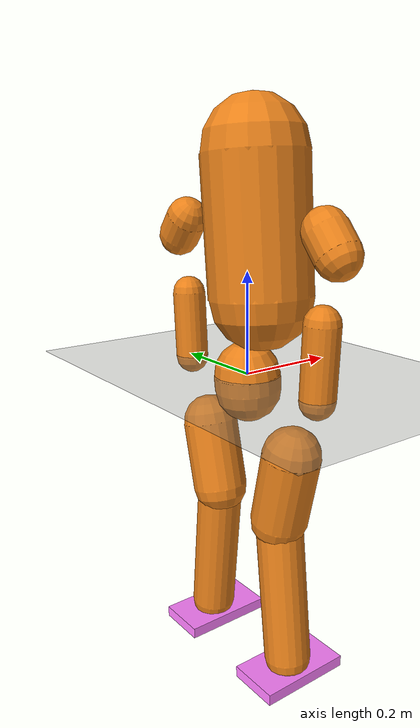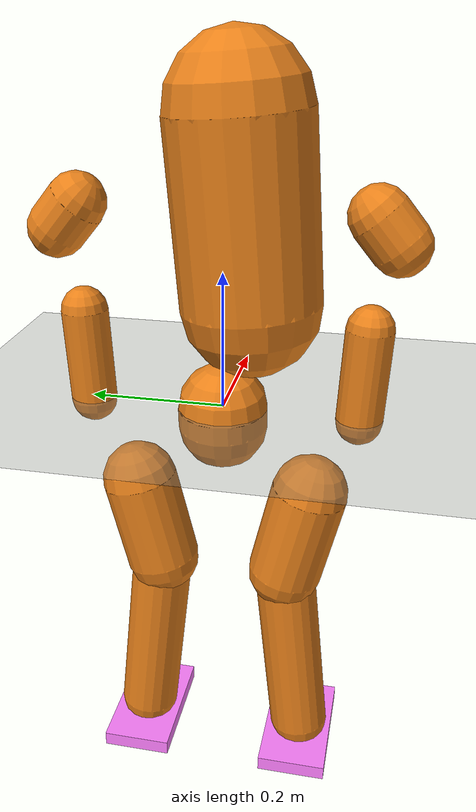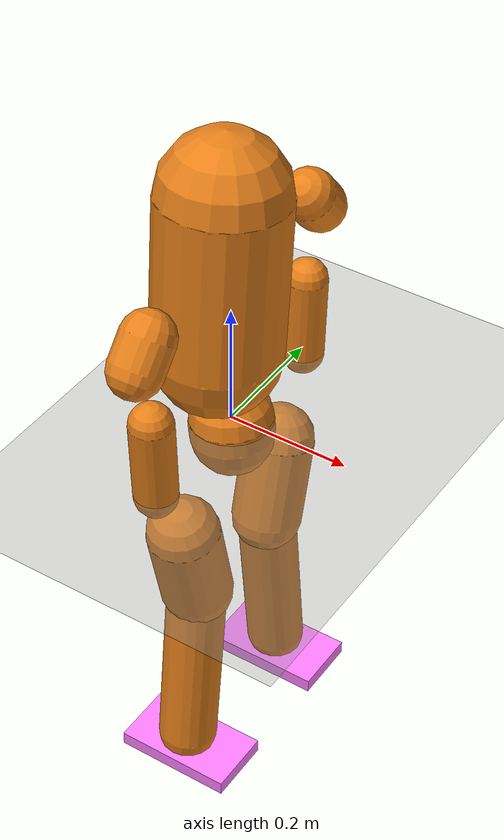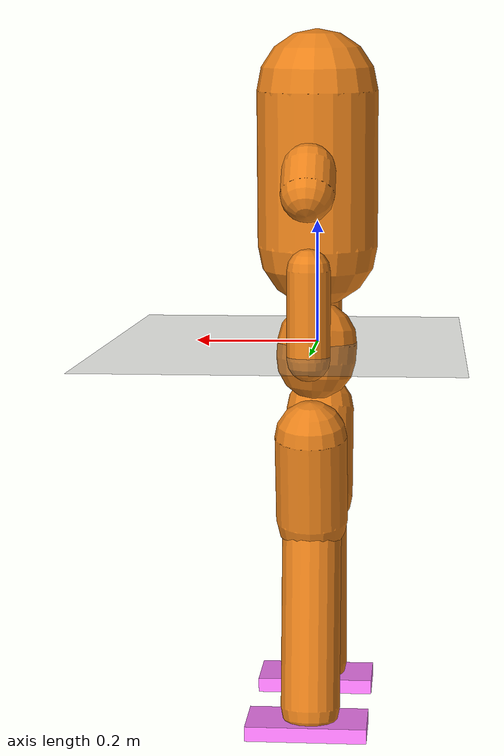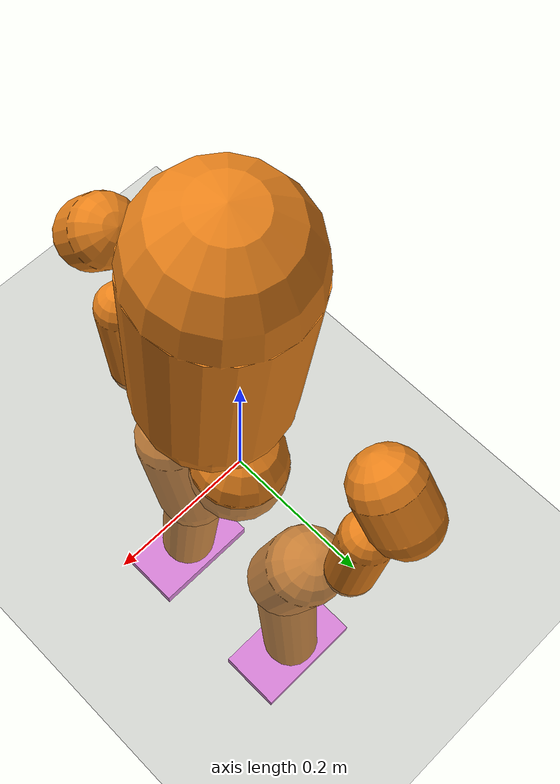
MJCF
<mujoco model="x1_sim">
  <option timestep="0.005" />
  <compiler angle="radian" />
  <default>
    <motor ctrlrange="-1 1" ctrllimited="true" gear="1" />
  </default>
  <worldbody>
    <body name="base_link" pos="0 0 0">
      <inertial pos="0.00252285 -0.00063439 0.03023409" mass="4.3041648" quat="-0.49993409 0.50022042 0.50515004 -0.49464013" diaginertia="0.01083013 0.021810116 0.026806174" />
      <freejoint name="floating_base" />
      <geom name="base_link_col" type="capsule" fromto="0 0 0 0.00245 0 -0.03" size="0.066" density="0" contype="1" conaffinity="1" friction="1.0 0.05 0.05" condim="4" rgba="0.9 0.5 0.1 1" group="1" />
      <body name="lumbar_yaw_link" pos="0.00245 0 0.11553403" quat="1 0 0 -2.274557e-05">
        <inertial pos="-0.01800066 1.4e-06 0.02432982" mass="0.36251906" quat="0.99348394 2.3462644e-05 0.11397217 -1.2536067e-05" diaginertia="0.00034245685 0.00045823 0.00065509315" />
        <joint name="lumbar_yaw_joint" type="hinge" limited="true" pos="0 0 0" axis="0 0 1" range="-1.0000 1.0000" stiffness="0" damping="0" armature="0.02" frictionloss="3.0" />
        <body name="lumbar_roll_link" pos="0 0 0.0405" quat="0.5 0.5 -0.5 -0.5">
          <inertial pos="-0.00029919 0.0003642 -0.00019197" mass="0.03412073" quat="0.53529739 0.56270362 0.3392439 -0.53078707" diaginertia="4.8125283e-06 4.9030789e-06 5.4643928e-06" />
          <joint name="lumbar_roll_joint" type="hinge" limited="true" pos="0 0 0" axis="0 0 1" range="-0.2500 0.2500" stiffness="0" damping="0" armature="0.02" frictionloss="3.0" />
          <body name="lumbar_pitch_link" pos="0 0 0" quat="0.70710678 0 0.70710678 0">
            <inertial pos="0.00070244 0.21815812 -0.00117164" mass="9.1971074" quat="-0.48427463 -0.49573294 0.50954022 0.50999579" diaginertia="0.060694152 0.12392505 0.16020602" />
            <joint name="lumbar_pitch_joint" type="hinge" limited="true" pos="0 0 0" axis="0 0 -1" range="-0.1500 0.4500" stiffness="0" damping="0" armature="0.02" frictionloss="4.0" />
            <geom name="lumbar_pitch_link_col" type="capsule" fromto="0 0 0.04 0 0.256 0.02" size="0.1" density="0" contype="1" conaffinity="1" friction="1.0 0.05 0.05" condim="4" rgba="0.9 0.5 0.1 1" group="1" />
            <body name="left_shoulder_pitch_link" pos="0 0.256 -0.1458" quat="0 0 0 -1" gravcomp="0">
              <inertial pos="-0.00251212 -0.00149141 -0.05674475" mass="1.0067875" quat="-0.67979561 -0.055012575 0.72872618 -0.061722725" diaginertia="0.0008533978 0.00095816181 0.0010856204" />
              <joint name="left_shoulder_pitch_joint" type="hinge" limited="true" pos="0 0 0" axis="0 0 -1" range="-2.5000 1.5000" stiffness="0" damping="0" armature="0.01" frictionloss="0.5" />
              <body name="left_shoulder_roll_link" pos="-0.0313 0 -0.0592" quat="0.70710548 0 -0.70710808 0" gravcomp="0">
                <inertial pos="0.000154 0.07784637 -0.02711338" mass="0.69169508" quat="-0.53585784 -0.46185342 0.5464353 0.44828145" diaginertia="0.00063698245 0.0011961138 0.0013367737" />
                <joint name="left_shoulder_roll_joint" type="hinge" limited="true" pos="0 0 0" axis="0 0 -1" range="-2.0000 0.0000" stiffness="0" damping="0" armature="0.01" frictionloss="0.5" />
                <body name="left_shoulder_yaw_link" pos="0 0.1252 -0.0313" quat="0.5 0.5 0.5 -0.5" gravcomp="0">
                  <inertial pos="-2.68e-06 0.00182113 -0.00392718" mass="0.72559372" quat="-0.46931073 0.5297545 -0.51442063 -0.48423033" diaginertia="0.0004812039 0.0011604112 0.0011833549" />
                  <joint name="left_shoulder_yaw_joint" type="hinge" limited="true" pos="0 0 0" axis="0 0 1" range="-1.8000 1.8000" stiffness="0" damping="0" armature="0.01" frictionloss="0.5" />
                  <geom name="left_shoulder_yaw_link_col" type="capsule" fromto="0 0 0 0 -0.031 -0.0365" size="0.042" density="0" contype="1" conaffinity="1" friction="1.0 0.05 0.05" condim="4" rgba="0.9 0.5 0.1 1" group="1" />
                  <body name="left_elbow_pitch_link" pos="0 -0.031 -0.0365" quat="0.70710678 -0.70710678 0 0" gravcomp="0">
                    <inertial pos="2.604e-05 0.07528242 0.0268658" mass="0.69780135" quat="0.42216492 0.56749847 -0.42219566 -0.56698597" diaginertia="0.00061435924 0.0010006506 0.0011626702" />
                    <joint name="left_elbow_pitch_joint" type="hinge" limited="true" pos="0 0 0" axis="0 0 1" range="0.0000 2.0000" stiffness="0" damping="0" armature="0.01" frictionloss="0.5" />
                    <body name="left_elbow_yaw_link" pos="0 0.117 0.031" quat="0.49999908 0.49999908 -0.50000092 0.50000092" gravcomp="0">
                      <inertial pos="3.656e-05 0.00424199 -0.05421422" mass="0.28787886" quat="0.70530782 0.060241355 -0.70390283 -0.058588874" diaginertia="0.00054032221 0.0007024769 0.00071486088" />
                      <joint name="left_elbow_yaw_joint" type="hinge" limited="true" pos="0 0 0" axis="0 0 1" range="-1.8000 1.8000" stiffness="0" damping="0" armature="0.01" frictionloss="0.5" />
                      <geom name="left_elbow_yaw_link_col" type="capsule" fromto="0 0 0 0.006 9.9998e-05 -0.1394" size="0.034" density="0" contype="1" conaffinity="1" friction="1.0 0.05 0.05" condim="4" rgba="0.9 0.5 0.1 1" group="1" />
                      <body name="left_wrist_pitch_link" pos="0.006 9.9998e-05 -0.1394" quat="0.62160997 0.78332691 0 0" gravcomp="0">
                        <inertial pos="-9.994e-05 0 0.00229425" mass="0.00900738" quat="0 0 0.70710678 0.70710678" diaginertia="2.4e-07 3.8e-07 5.7e-07" />
                        <joint name="left_wrist_pitch_joint" type="hinge" limited="true" pos="0 0 0" axis="1 0 0" range="-0.4000 0.4000" stiffness="0" damping="0" armature="0.005" frictionloss="0.2" />
                        <body name="left_wrist_roll_link" pos="0 0 0" quat="0.73068165 -0.61544466 0.19037934 -0.22602632" gravcomp="0">
                          <inertial pos="-0.019731143 0.0013385766 -0.032177575" mass="0.370899" quat="-0.16415344 -0.35401035 0.43660468 0.81062116" diaginertia="0.000211598 0.000356841 0.000404077" />
                          <joint name="left_wrist_roll_joint" type="hinge" limited="true" pos="0 0 0" axis="0 1 0" range="-0.4000 0.4000" stiffness="0" damping="0" armature="0.005" frictionloss="0.2" />
                          <site name="x_lhand" size="0.005" />
                        </body>
                      </body>
                    </body>
                  </body>
                </body>
              </body>
            </body>
            <body name="right_shoulder_pitch_link" pos="0 0.256 0.1458" quat="-3.6732051e-06 1 0 0" gravcomp="0">
              <inertial pos="0.00250704 -0.00149173 -0.05674328" mass="1.0067875" quat="0.72873245 -0.062328101 -0.67979179 -0.054289459" diaginertia="0.00085339593 0.00095816816 0.0010856159" />
              <joint name="right_shoulder_pitch_joint" type="hinge" limited="true" pos="0 0 0" axis="0 0 1" range="-2.5000 1.5000" stiffness="0" damping="0" armature="0.01" frictionloss="0.5" />
              <body name="right_shoulder_roll_link" pos="0.0313 0 -0.0592" quat="-2.5973435e-06 0.70710548 2.597353e-06 0.70710808" gravcomp="0">
                <inertial pos="9.998e-05 -0.07787239 -0.02705625" mass="0.69142604" quat="-0.4594695 -0.53694627 0.45064727 0.54542967" diaginertia="0.00063629365 0.0011970435 0.0013376129" />
                <joint name="right_shoulder_roll_joint" type="hinge" limited="true" pos="0 0 0" axis="0 0 1" range="-2.0000 0.0000" stiffness="0" damping="0" armature="0.01" frictionloss="0.5" />
                <body name="right_shoulder_yaw_link" pos="0 -0.1252 -0.0313" quat="0.70710548 0.70710808 0 0" gravcomp="0">
                  <inertial pos="-0.00189082 -0.00017102 0.03175107" mass="0.604503" quat="0.61216355 0.63014189 0.32261048 -0.35227755" diaginertia="0.00049190455 0.00050515813 0.00055056732" />
                  <joint name="right_shoulder_yaw_joint" type="hinge" limited="true" pos="0 0 0" axis="0 0 1" range="-1.8000 1.8000" stiffness="0" damping="0" armature="0.01" frictionloss="0.5" />
                  <geom name="right_shoulder_yaw_link_col" type="capsule" fromto="0 0 0 -0.031 0 0.0365" size="0.042" density="0" contype="1" conaffinity="1" friction="1.0 0.05 0.05" condim="4" rgba="0.9 0.5 0.1 1" group="1" />
                  <body name="right_elbow_pitch_link" pos="-0.031 0 0.0365" quat="0.5 -0.5 0.5 -0.5" gravcomp="0">
                    <inertial pos="-2.604e-05 -0.07529828 0.02685625" mass="0.69780135" quat="0.56738015 0.42232355 -0.56686736 -0.42235527" diaginertia="0.00061417119 0.0010011586 0.0011630202" />
                    <joint name="right_elbow_pitch_joint" type="hinge" limited="true" pos="0 0 0" axis="0 0 -1" range="0.0000 2.0000" stiffness="0" damping="0" armature="0.01" frictionloss="0.5" />
                    <body name="right_elbow_yaw_link" pos="0 -0.117 0.031" quat="0.49999908 -0.49999908 -0.50000092 -0.50000092" gravcomp="0">
                      <inertial pos="-3.65e-05 -0.00422926 -0.05414537" mass="0.28835476" quat="0.060262671 0.70530237 -0.058608682 -0.70390483" diaginertia="0.00054035512 0.000703364 0.00071572088" />
                      <joint name="right_elbow_yaw_joint" type="hinge" limited="true" pos="0 0 0" axis="0 0 -1" range="-1.8000 1.8000" stiffness="0" damping="0" armature="0.01" frictionloss="0.5" />
                      <geom name="right_elbow_yaw_link_col" type="capsule" fromto="0 0 0 0.006 9.9998e-05 -0.1394" size="0.034" density="0" contype="1" conaffinity="1" friction="1.0 0.05 0.05" condim="4" rgba="0.9 0.5 0.1 1" group="1" />
                      <body name="right_wrist_pitch_link" pos="0.006 9.9998e-05 -0.1394" quat="0.62160997 0.78332691 0 0" gravcomp="0">
                        <inertial pos="-9.994e-05 0 0.00229425" mass="0.00900738" quat="0 0 0.70710678 0.70710678" diaginertia="2.4e-07 3.8e-07 5.7e-07" />
                        <joint name="right_wrist_pitch_joint" type="hinge" limited="true" pos="0 0 0" axis="1 0 0" range="-0.4000 0.4000" stiffness="0" damping="0" armature="0.005" frictionloss="0.2" />
                        <body name="right_wrist_roll_link" pos="0 0 0" quat="0.73068165 -0.61544466 0.19037934 -0.22602632" gravcomp="0">
                          <inertial pos="-0.020122254 -0.025856909 -0.01878886" mass="0.370899" quat="0.17406994 0.50719397 -0.29774186 0.78981245" diaginertia="0.000211598 0.000356841 0.000404077" />
                          <joint name="right_wrist_roll_joint" type="hinge" limited="true" pos="0 0 0" axis="0 1 0" range="-0.4000 0.4000" stiffness="0" damping="0" armature="0.005" frictionloss="0.2" />
                          <site name="x_rhand" size="0.005" />
                        </body>
                      </body>
                    </body>
                  </body>
                </body>
              </body>
            </body>
            <site name="x_torso" size="0.005" />
          </body>
        </body>
      </body>
      <body name="left_hip_pitch_link" pos="0.00245 0.092277 -0.012143" quat="0.65328003 0.27059915 -0.27059815 0.65328243" gravcomp="0">
        <inertial pos="-4.816e-05 -0.01075844 -0.05407776" mass="1.6733645" quat="-0.55583853 -0.41053313 -0.43015369 0.58092502" diaginertia="0.0021514249 0.0023446612 0.0025641839" />
        <joint name="left_hip_pitch_joint" type="hinge" limited="true" pos="0 0 0" axis="0 0 1" range="-1.0000 2.0000" stiffness="0" damping="0" armature="0.02" frictionloss="4.0" />
        <body name="left_hip_roll_link" pos="0 -0.0405 -0.0589" quat="0.65328148 0.65328148 0.27059805 -0.27059805" gravcomp="0">
          <inertial pos="0.00014604 -0.04123483 -0.01015339" mass="0.28562185" quat="-0.23594177 0.6650998 0.66693304 0.23911095" diaginertia="0.00027528831 0.00055729377 0.00061295792" />
          <joint name="left_hip_roll_joint" type="hinge" limited="true" pos="0 0 0" axis="0 0 -1" range="-1.5000 0.2000" stiffness="0" damping="0" armature="0.02" frictionloss="3.0" />
          <body name="left_hip_yaw_link" pos="0 -0.083804916 -0.0406" quat="0.70710678 0.70710678 0 0" gravcomp="0">
            <inertial pos="-0.00212295 -3.062e-05 0.09164842" mass="2.7369623" quat="-0.68378267 0.0022403155 0.72967696 0.0027883451" diaginertia="0.0033874369 0.012449468 0.012747356" />
            <joint name="left_hip_yaw_joint" type="hinge" limited="true" pos="0 0 0" axis="0 0 -1" range="-1.5000 1.5000" stiffness="0" damping="0" armature="0.02" frictionloss="3.0" />
            <geom name="left_hip_yaw_link_col" type="capsule" fromto="0 0 0 -0.0337 0 0.1422" size="0.058" density="0" contype="1" conaffinity="1" friction="1.0 0.05 0.05" condim="4" rgba="0.9 0.5 0.1 1" group="1" />
            <body name="left_knee_pitch_link" pos="-0.0337 0 0.1422" quat="0.5 -0.5 0.5 -0.5" gravcomp="0">
              <inertial pos="-0.0047354 -0.13101324 0.0279688" mass="1.5122608" quat="0.71028505 -0.016246061 0.079548123 0.69921621" diaginertia="0.0016206203 0.0080646226 0.0083828071" />
              <joint name="left_knee_pitch_joint" type="hinge" limited="true" pos="0 0 0" axis="0 0 1" range="0.0000 2.0000" stiffness="0" damping="0" armature="0.02" frictionloss="4.0" />
              <geom name="left_knee_pitch_link_col" type="capsule" fromto="0 0 0 0 -0.30494 0.0336" size="0.048" density="0" contype="1" conaffinity="1" friction="1.0 0.05 0.05" condim="4" rgba="0.9 0.5 0.1 1" group="1" />
              <body name="left_ankle_pitch_link" pos="0 -0.30494 0.0336" quat="0 0 -1 0" gravcomp="0">
                <inertial pos="-2.32e-06 7.077e-05 -2.048e-05" mass="0.06217211" quat="-0.5 0.5 0.5 0.5" diaginertia="6.68e-06 2.273e-05 2.373e-05" />
                <joint name="left_ankle_pitch_joint" type="hinge" limited="true" pos="0 0 0" axis="0 0 -1" range="-0.4100 0.3500" stiffness="0" damping="0" armature="0.02" frictionloss="1.5" />
                <body name="left_ankle_roll_link" pos="0 0 0" quat="0.70710678 0 0.70710678 0" gravcomp="0">
                  <inertial pos="0.00017156 -0.02524695 -0.00019936" mass="0.58971207" quat="-0.50741897 0.49044917 0.49158279 0.51022737" diaginertia="0.00054139113 0.0015211445 0.0019006944" />
                  <joint name="left_ankle_roll_joint" type="hinge" limited="true" pos="0 0 0" axis="0 0 1" range="-0.6400 0.6400" stiffness="0" damping="0" armature="0.02" frictionloss="1.5" />
                  <geom name="left_ankle_roll_link_sole" type="box" pos="0 -0.0303 0.005" size="0.055 0.012 0.098" density="0" contype="1" conaffinity="1" friction="1.0 0.05 0.05" condim="4" rgba="1 0.5 1 1" group="1" />
                  <site name="x_lfoot" size="0.005" />
                </body>
              </body>
            </body>
          </body>
        </body>
      </body>
      <body name="right_hip_pitch_link" pos="0.00245 -0.092277 -0.012143" quat="0.65328003 -0.27059915 -0.27059815 -0.65328243" gravcomp="0">
        <inertial pos="-0.00011915 0.01061483 -0.05407727" mass="1.6665735" quat="0.5736407 -0.43321111 -0.40738862 -0.56329298" diaginertia="0.0021331293 0.0023212051 0.0025451856" />
        <joint name="right_hip_pitch_joint" type="hinge" limited="true" pos="0 0 0" axis="0 0 1" range="-2.0000 1.0000" stiffness="0" damping="0" armature="0.02" frictionloss="4.0" />
        <body name="right_hip_roll_link" pos="0 0.0405 -0.0589" quat="0.65328148 0.65328148 0.27059805 -0.27059805" gravcomp="0">
          <inertial pos="-0.00027058 -0.04164617 0.01034263" mass="0.28768793" quat="-0.66237136 0.22470499 0.24666334 0.6707675" diaginertia="0.00028038909 0.00056679462 0.00062656629" />
          <joint name="right_hip_roll_joint" type="hinge" limited="true" pos="0 0 0" axis="0 0 1" range="-0.2000 1.5000" stiffness="0" damping="0" armature="0.02" frictionloss="3.0" />
          <body name="right_hip_yaw_link" pos="0 -0.077754916 0.0406" quat="0.70710023 -0.70710023 -0.0030441826 0.0030441826" gravcomp="0">
            <inertial pos="-0.00241642 1.672e-05 -0.09704704" mass="2.6963535" quat="0.00054247237 -0.68390305 0.00090981878 0.72957213" diaginertia="0.003325326 0.01225062 0.012579424" />
            <joint name="right_hip_yaw_joint" type="hinge" limited="true" pos="0 0 0" axis="0 0 1" range="-1.5000 1.5000" stiffness="0" damping="0" armature="0.02" frictionloss="3.0" />
            <geom name="right_hip_yaw_link_col" type="capsule" fromto="0 0 0 -0.0347752 0 -0.147956" size="0.058" density="0" contype="1" conaffinity="1" friction="1.0 0.05 0.05" condim="4" rgba="0.9 0.5 0.1 1" group="1" />
            <body name="right_knee_pitch_link" pos="-0.034775216 0 -0.14795606" quat="0.4978428 0.50214793 0.50214793 0.4978428" gravcomp="0">
              <inertial pos="0.00477062 -0.13172342 0.02793834" mass="1.50954" quat="0.70923015 -0.016207092 -0.079956259 -0.70024062" diaginertia="0.0016171475 0.0080198498 0.0083387026" />
              <joint name="right_knee_pitch_joint" type="hinge" limited="true" pos="0 0 0" axis="0 0 -1" range="0.0000 2.0000" stiffness="0" damping="0" armature="0.02" frictionloss="4.0" />
              <geom name="right_knee_pitch_link_col" type="capsule" fromto="0 0 0 0 -0.30494 0.0336" size="0.048" density="0" contype="1" conaffinity="1" friction="1.0 0.05 0.05" condim="4" rgba="0.9 0.5 0.1 1" group="1" />
              <body name="right_ankle_pitch_link" pos="0 -0.30494 0.0336" quat="0 1 0 0" gravcomp="0">
                <inertial pos="2.47e-06 -7.076e-05 -1.763e-05" mass="0.06217211" quat="-0.50014661 -0.49985335 -0.49985335 0.50014661" diaginertia="6.6799941e-06 2.273e-05 2.3730006e-05" />
                <joint name="right_ankle_pitch_joint" type="hinge" limited="true" pos="0 0 0" axis="0 0 1" range="-0.4100 0.3500" stiffness="0" damping="0" armature="0.02" frictionloss="1.5" />
                <body name="right_ankle_roll_link" pos="0 0 0" quat="0.70710678 0 0.70710678 0" gravcomp="0">
                  <inertial pos="-2.32e-06 0.02507893 0.00010556" mass="0.59182763" quat="-0.49119535 0.50862693 0.50864236 0.49123185" diaginertia="0.00054236958 0.00151845 0.0018940604" />
                  <joint name="right_ankle_roll_joint" type="hinge" limited="true" pos="0 0 0" axis="0 0 1" range="-0.6400 0.6400" stiffness="0" damping="0" armature="0.02" frictionloss="1.5" />
                  <geom name="right_ankle_roll_link_sole" type="box" pos="0 0.0303 0.005" size="0.055 0.012 0.098" density="0" contype="1" conaffinity="1" friction="1.0 0.05 0.05" condim="4" rgba="1 0.5 1 1" group="1" />
                  <site name="x_rfoot" size="0.005" />
                </body>
              </body>
            </body>
          </body>
        </body>
      </body>
      <site name="x_base" size="0.005" />
    </body>
    <geom name="floor" type="plane" size="0 3 0.125" contype="1" conaffinity="1" friction="1.0 0.05 0.05" condim="4" />
    <light pos="0 0 3" dir="0 0 -1" directional="true" />
  </worldbody>
  <contact>
    <exclude body1="base_link" body2="lumbar_yaw_link" />
    <exclude body1="base_link" body2="lumbar_roll_link" />
    <exclude body1="base_link" body2="left_hip_pitch_link" />
    <exclude body1="base_link" body2="left_hip_roll_link" />
    <exclude body1="base_link" body2="right_hip_pitch_link" />
    <exclude body1="base_link" body2="right_hip_roll_link" />
    <exclude body1="lumbar_yaw_link" body2="lumbar_roll_link" />
    <exclude body1="lumbar_yaw_link" body2="lumbar_pitch_link" />
    <exclude body1="lumbar_yaw_link" body2="left_hip_pitch_link" />
    <exclude body1="lumbar_yaw_link" body2="right_hip_pitch_link" />
    <exclude body1="lumbar_roll_link" body2="lumbar_pitch_link" />
    <exclude body1="lumbar_roll_link" body2="left_shoulder_pitch_link" />
    <exclude body1="lumbar_roll_link" body2="right_shoulder_pitch_link" />
    <exclude body1="lumbar_pitch_link" body2="left_shoulder_pitch_link" />
    <exclude body1="lumbar_pitch_link" body2="left_shoulder_roll_link" />
    <exclude body1="lumbar_pitch_link" body2="right_shoulder_pitch_link" />
    <exclude body1="lumbar_pitch_link" body2="right_shoulder_roll_link" />
    <exclude body1="left_shoulder_pitch_link" body2="left_shoulder_roll_link" />
    <exclude body1="left_shoulder_pitch_link" body2="left_shoulder_yaw_link" />
    <exclude body1="left_shoulder_pitch_link" body2="right_shoulder_pitch_link" />
    <exclude body1="left_shoulder_roll_link" body2="left_shoulder_yaw_link" />
    <exclude body1="left_shoulder_roll_link" body2="left_elbow_pitch_link" />
    <exclude body1="left_shoulder_yaw_link" body2="left_elbow_pitch_link" />
    <exclude body1="left_shoulder_yaw_link" body2="left_elbow_yaw_link" />
    <exclude body1="left_elbow_pitch_link" body2="left_elbow_yaw_link" />
    <exclude body1="left_elbow_pitch_link" body2="left_wrist_pitch_link" />
    <exclude body1="left_elbow_yaw_link" body2="left_wrist_pitch_link" />
    <exclude body1="left_elbow_yaw_link" body2="left_wrist_roll_link" />
    <exclude body1="left_wrist_pitch_link" body2="left_wrist_roll_link" />
    <exclude body1="right_shoulder_pitch_link" body2="right_shoulder_roll_link" />
    <exclude body1="right_shoulder_pitch_link" body2="right_shoulder_yaw_link" />
    <exclude body1="right_shoulder_roll_link" body2="right_shoulder_yaw_link" />
    <exclude body1="right_shoulder_roll_link" body2="right_elbow_pitch_link" />
    <exclude body1="right_shoulder_yaw_link" body2="right_elbow_pitch_link" />
    <exclude body1="right_shoulder_yaw_link" body2="right_elbow_yaw_link" />
    <exclude body1="right_elbow_pitch_link" body2="right_elbow_yaw_link" />
    <exclude body1="right_elbow_pitch_link" body2="right_wrist_pitch_link" />
    <exclude body1="right_elbow_yaw_link" body2="right_wrist_pitch_link" />
    <exclude body1="right_elbow_yaw_link" body2="right_wrist_roll_link" />
    <exclude body1="right_wrist_pitch_link" body2="right_wrist_roll_link" />
    <exclude body1="left_hip_pitch_link" body2="left_hip_roll_link" />
    <exclude body1="left_hip_pitch_link" body2="left_hip_yaw_link" />
    <exclude body1="left_hip_pitch_link" body2="right_hip_pitch_link" />
    <exclude body1="left_hip_roll_link" body2="left_hip_yaw_link" />
    <exclude body1="left_hip_roll_link" body2="left_knee_pitch_link" />
    <exclude body1="left_hip_yaw_link" body2="left_knee_pitch_link" />
    <exclude body1="left_hip_yaw_link" body2="left_ankle_pitch_link" />
    <exclude body1="left_knee_pitch_link" body2="left_ankle_pitch_link" />
    <exclude body1="left_knee_pitch_link" body2="left_ankle_roll_link" />
    <exclude body1="left_ankle_pitch_link" body2="left_ankle_roll_link" />
    <exclude body1="right_hip_pitch_link" body2="right_hip_roll_link" />
    <exclude body1="right_hip_pitch_link" body2="right_hip_yaw_link" />
    <exclude body1="right_hip_roll_link" body2="right_hip_yaw_link" />
    <exclude body1="right_hip_roll_link" body2="right_knee_pitch_link" />
    <exclude body1="right_hip_yaw_link" body2="right_knee_pitch_link" />
    <exclude body1="right_hip_yaw_link" body2="right_ankle_pitch_link" />
    <exclude body1="right_knee_pitch_link" body2="right_ankle_pitch_link" />
    <exclude body1="right_knee_pitch_link" body2="right_ankle_roll_link" />
    <exclude body1="right_ankle_pitch_link" body2="right_ankle_roll_link" />
    <exclude body1="base_link" body2="lumbar_yaw_link" />
    <exclude body1="base_link" body2="lumbar_roll_link" />
    <exclude body1="base_link" body2="lumbar_pitch_link" />
    <exclude body1="base_link" body2="left_shoulder_pitch_link" />
    <exclude body1="base_link" body2="left_shoulder_roll_link" />
    <exclude body1="base_link" body2="left_shoulder_yaw_link" />
    <exclude body1="base_link" body2="left_elbow_pitch_link" />
    <exclude body1="base_link" body2="left_elbow_yaw_link" />
    <exclude body1="base_link" body2="left_wrist_pitch_link" />
    <exclude body1="base_link" body2="left_wrist_roll_link" />
    <exclude body1="base_link" body2="right_shoulder_pitch_link" />
    <exclude body1="base_link" body2="right_shoulder_roll_link" />
    <exclude body1="base_link" body2="right_shoulder_yaw_link" />
    <exclude body1="base_link" body2="right_elbow_pitch_link" />
    <exclude body1="base_link" body2="right_elbow_yaw_link" />
    <exclude body1="base_link" body2="right_wrist_pitch_link" />
    <exclude body1="base_link" body2="right_wrist_roll_link" />
    <exclude body1="base_link" body2="left_hip_pitch_link" />
    <exclude body1="base_link" body2="left_hip_roll_link" />
    <exclude body1="base_link" body2="left_hip_yaw_link" />
    <exclude body1="base_link" body2="left_knee_pitch_link" />
    <exclude body1="base_link" body2="left_ankle_pitch_link" />
    <exclude body1="base_link" body2="left_ankle_roll_link" />
    <exclude body1="base_link" body2="right_hip_pitch_link" />
    <exclude body1="base_link" body2="right_hip_roll_link" />
    <exclude body1="base_link" body2="right_hip_yaw_link" />
    <exclude body1="base_link" body2="right_knee_pitch_link" />
    <exclude body1="base_link" body2="right_ankle_pitch_link" />
    <exclude body1="base_link" body2="right_ankle_roll_link" />
    <exclude body1="lumbar_yaw_link" body2="lumbar_roll_link" />
    <exclude body1="lumbar_yaw_link" body2="lumbar_pitch_link" />
    <exclude body1="lumbar_yaw_link" body2="left_shoulder_pitch_link" />
    <exclude body1="lumbar_yaw_link" body2="left_shoulder_roll_link" />
    <exclude body1="lumbar_yaw_link" body2="left_shoulder_yaw_link" />
    <exclude body1="lumbar_yaw_link" body2="left_elbow_pitch_link" />
    <exclude body1="lumbar_yaw_link" body2="left_elbow_yaw_link" />
    <exclude body1="lumbar_yaw_link" body2="left_wrist_pitch_link" />
    <exclude body1="lumbar_yaw_link" body2="left_wrist_roll_link" />
    <exclude body1="lumbar_yaw_link" body2="right_shoulder_pitch_link" />
    <exclude body1="lumbar_yaw_link" body2="right_shoulder_roll_link" />
    <exclude body1="lumbar_yaw_link" body2="right_shoulder_yaw_link" />
    <exclude body1="lumbar_yaw_link" body2="right_elbow_pitch_link" />
    <exclude body1="lumbar_yaw_link" body2="right_elbow_yaw_link" />
    <exclude body1="lumbar_yaw_link" body2="right_wrist_pitch_link" />
    <exclude body1="lumbar_yaw_link" body2="right_wrist_roll_link" />
    <exclude body1="lumbar_yaw_link" body2="left_hip_pitch_link" />
    <exclude body1="lumbar_yaw_link" body2="left_hip_roll_link" />
    <exclude body1="lumbar_yaw_link" body2="left_hip_yaw_link" />
    <exclude body1="lumbar_yaw_link" body2="left_knee_pitch_link" />
    <exclude body1="lumbar_yaw_link" body2="left_ankle_pitch_link" />
    <exclude body1="lumbar_yaw_link" body2="left_ankle_roll_link" />
    <exclude body1="lumbar_yaw_link" body2="right_hip_pitch_link" />
    <exclude body1="lumbar_yaw_link" body2="right_hip_roll_link" />
    <exclude body1="lumbar_yaw_link" body2="right_hip_yaw_link" />
    <exclude body1="lumbar_yaw_link" body2="right_knee_pitch_link" />
    <exclude body1="lumbar_yaw_link" body2="right_ankle_pitch_link" />
    <exclude body1="lumbar_yaw_link" body2="right_ankle_roll_link" />
    <exclude body1="lumbar_roll_link" body2="lumbar_pitch_link" />
    <exclude body1="lumbar_roll_link" body2="left_shoulder_pitch_link" />
    <exclude body1="lumbar_roll_link" body2="left_shoulder_roll_link" />
    <exclude body1="lumbar_roll_link" body2="left_shoulder_yaw_link" />
    <exclude body1="lumbar_roll_link" body2="left_elbow_pitch_link" />
    <exclude body1="lumbar_roll_link" body2="left_elbow_yaw_link" />
    <exclude body1="lumbar_roll_link" body2="left_wrist_pitch_link" />
    <exclude body1="lumbar_roll_link" body2="left_wrist_roll_link" />
    <exclude body1="lumbar_roll_link" body2="right_shoulder_pitch_link" />
    <exclude body1="lumbar_roll_link" body2="right_shoulder_roll_link" />
    <exclude body1="lumbar_roll_link" body2="right_shoulder_yaw_link" />
    <exclude body1="lumbar_roll_link" body2="right_elbow_pitch_link" />
    <exclude body1="lumbar_roll_link" body2="right_elbow_yaw_link" />
    <exclude body1="lumbar_roll_link" body2="right_wrist_pitch_link" />
    <exclude body1="lumbar_roll_link" body2="right_wrist_roll_link" />
    <exclude body1="lumbar_roll_link" body2="left_hip_pitch_link" />
    <exclude body1="lumbar_roll_link" body2="left_hip_roll_link" />
    <exclude body1="lumbar_roll_link" body2="left_hip_yaw_link" />
    <exclude body1="lumbar_roll_link" body2="left_knee_pitch_link" />
    <exclude body1="lumbar_roll_link" body2="left_ankle_pitch_link" />
    <exclude body1="lumbar_roll_link" body2="left_ankle_roll_link" />
    <exclude body1="lumbar_roll_link" body2="right_hip_pitch_link" />
    <exclude body1="lumbar_roll_link" body2="right_hip_roll_link" />
    <exclude body1="lumbar_roll_link" body2="right_hip_yaw_link" />
    <exclude body1="lumbar_roll_link" body2="right_knee_pitch_link" />
    <exclude body1="lumbar_roll_link" body2="right_ankle_pitch_link" />
    <exclude body1="lumbar_roll_link" body2="right_ankle_roll_link" />
    <exclude body1="lumbar_pitch_link" body2="left_shoulder_pitch_link" />
    <exclude body1="lumbar_pitch_link" body2="left_shoulder_roll_link" />
    <exclude body1="lumbar_pitch_link" body2="left_shoulder_yaw_link" />
    <exclude body1="lumbar_pitch_link" body2="left_elbow_pitch_link" />
    <exclude body1="lumbar_pitch_link" body2="left_elbow_yaw_link" />
    <exclude body1="lumbar_pitch_link" body2="left_wrist_pitch_link" />
    <exclude body1="lumbar_pitch_link" body2="left_wrist_roll_link" />
    <exclude body1="lumbar_pitch_link" body2="right_shoulder_pitch_link" />
    <exclude body1="lumbar_pitch_link" body2="right_shoulder_roll_link" />
    <exclude body1="lumbar_pitch_link" body2="right_shoulder_yaw_link" />
    <exclude body1="lumbar_pitch_link" body2="right_elbow_pitch_link" />
    <exclude body1="lumbar_pitch_link" body2="right_elbow_yaw_link" />
    <exclude body1="lumbar_pitch_link" body2="right_wrist_pitch_link" />
    <exclude body1="lumbar_pitch_link" body2="right_wrist_roll_link" />
    <exclude body1="lumbar_pitch_link" body2="left_hip_pitch_link" />
    <exclude body1="lumbar_pitch_link" body2="left_hip_roll_link" />
    <exclude body1="lumbar_pitch_link" body2="left_hip_yaw_link" />
    <exclude body1="lumbar_pitch_link" body2="left_knee_pitch_link" />
    <exclude body1="lumbar_pitch_link" body2="left_ankle_pitch_link" />
    <exclude body1="lumbar_pitch_link" body2="left_ankle_roll_link" />
    <exclude body1="lumbar_pitch_link" body2="right_hip_pitch_link" />
    <exclude body1="lumbar_pitch_link" body2="right_hip_roll_link" />
    <exclude body1="lumbar_pitch_link" body2="right_hip_yaw_link" />
    <exclude body1="lumbar_pitch_link" body2="right_knee_pitch_link" />
    <exclude body1="lumbar_pitch_link" body2="right_ankle_pitch_link" />
    <exclude body1="lumbar_pitch_link" body2="right_ankle_roll_link" />
    <exclude body1="left_shoulder_pitch_link" body2="left_shoulder_roll_link" />
    <exclude body1="left_shoulder_pitch_link" body2="left_shoulder_yaw_link" />
    <exclude body1="left_shoulder_pitch_link" body2="left_elbow_pitch_link" />
    <exclude body1="left_shoulder_pitch_link" body2="left_elbow_yaw_link" />
    <exclude body1="left_shoulder_pitch_link" body2="left_wrist_pitch_link" />
    <exclude body1="left_shoulder_pitch_link" body2="left_wrist_roll_link" />
    <exclude body1="left_shoulder_pitch_link" body2="right_shoulder_pitch_link" />
    <exclude body1="left_shoulder_pitch_link" body2="right_shoulder_roll_link" />
    <exclude body1="left_shoulder_pitch_link" body2="right_shoulder_yaw_link" />
    <exclude body1="left_shoulder_pitch_link" body2="right_elbow_pitch_link" />
    <exclude body1="left_shoulder_pitch_link" body2="right_elbow_yaw_link" />
    <exclude body1="left_shoulder_pitch_link" body2="right_wrist_pitch_link" />
    <exclude body1="left_shoulder_pitch_link" body2="right_wrist_roll_link" />
    <exclude body1="left_shoulder_pitch_link" body2="left_hip_pitch_link" />
    <exclude body1="left_shoulder_pitch_link" body2="left_hip_roll_link" />
    <exclude body1="left_shoulder_pitch_link" body2="left_hip_yaw_link" />
    <exclude body1="left_shoulder_pitch_link" body2="left_knee_pitch_link" />
    <exclude body1="left_shoulder_pitch_link" body2="left_ankle_pitch_link" />
    <exclude body1="left_shoulder_pitch_link" body2="left_ankle_roll_link" />
    <exclude body1="left_shoulder_pitch_link" body2="right_hip_pitch_link" />
    <exclude body1="left_shoulder_pitch_link" body2="right_hip_roll_link" />
    <exclude body1="left_shoulder_pitch_link" body2="right_hip_yaw_link" />
    <exclude body1="left_shoulder_pitch_link" body2="right_knee_pitch_link" />
    <exclude body1="left_shoulder_pitch_link" body2="right_ankle_pitch_link" />
    <exclude body1="left_shoulder_pitch_link" body2="right_ankle_roll_link" />
    <exclude body1="left_shoulder_roll_link" body2="left_shoulder_yaw_link" />
    <exclude body1="left_shoulder_roll_link" body2="left_elbow_pitch_link" />
    <exclude body1="left_shoulder_roll_link" body2="left_elbow_yaw_link" />
    <exclude body1="left_shoulder_roll_link" body2="left_wrist_pitch_link" />
    <exclude body1="left_shoulder_roll_link" body2="left_wrist_roll_link" />
    <exclude body1="left_shoulder_roll_link" body2="right_shoulder_pitch_link" />
    <exclude body1="left_shoulder_roll_link" body2="right_shoulder_roll_link" />
    <exclude body1="left_shoulder_roll_link" body2="right_shoulder_yaw_link" />
    <exclude body1="left_shoulder_roll_link" body2="right_elbow_pitch_link" />
    <exclude body1="left_shoulder_roll_link" body2="right_elbow_yaw_link" />
    <exclude body1="left_shoulder_roll_link" body2="right_wrist_pitch_link" />
    <exclude body1="left_shoulder_roll_link" body2="right_wrist_roll_link" />
    <exclude body1="left_shoulder_roll_link" body2="left_hip_pitch_link" />
    <exclude body1="left_shoulder_roll_link" body2="left_hip_roll_link" />
    <exclude body1="left_shoulder_roll_link" body2="left_hip_yaw_link" />
    <exclude body1="left_shoulder_roll_link" body2="left_knee_pitch_link" />
    <exclude body1="left_shoulder_roll_link" body2="left_ankle_pitch_link" />
    <exclude body1="left_shoulder_roll_link" body2="left_ankle_roll_link" />
    <exclude body1="left_shoulder_roll_link" body2="right_hip_pitch_link" />
    <exclude body1="left_shoulder_roll_link" body2="right_hip_roll_link" />
    <exclude body1="left_shoulder_roll_link" body2="right_hip_yaw_link" />
    <exclude body1="left_shoulder_roll_link" body2="right_knee_pitch_link" />
    <exclude body1="left_shoulder_roll_link" body2="right_ankle_pitch_link" />
    <exclude body1="left_shoulder_roll_link" body2="right_ankle_roll_link" />
    <exclude body1="left_shoulder_yaw_link" body2="left_elbow_pitch_link" />
    <exclude body1="left_shoulder_yaw_link" body2="left_elbow_yaw_link" />
    <exclude body1="left_shoulder_yaw_link" body2="left_wrist_pitch_link" />
    <exclude body1="left_shoulder_yaw_link" body2="left_wrist_roll_link" />
    <exclude body1="left_shoulder_yaw_link" body2="right_shoulder_pitch_link" />
    <exclude body1="left_shoulder_yaw_link" body2="right_shoulder_roll_link" />
    <exclude body1="left_shoulder_yaw_link" body2="right_shoulder_yaw_link" />
    <exclude body1="left_shoulder_yaw_link" body2="right_elbow_pitch_link" />
    <exclude body1="left_shoulder_yaw_link" body2="right_elbow_yaw_link" />
    <exclude body1="left_shoulder_yaw_link" body2="right_wrist_pitch_link" />
    <exclude body1="left_shoulder_yaw_link" body2="right_wrist_roll_link" />
    <exclude body1="left_shoulder_yaw_link" body2="left_hip_pitch_link" />
    <exclude body1="left_shoulder_yaw_link" body2="left_hip_roll_link" />
    <exclude body1="left_shoulder_yaw_link" body2="left_hip_yaw_link" />
    <exclude body1="left_shoulder_yaw_link" body2="left_knee_pitch_link" />
    <exclude body1="left_shoulder_yaw_link" body2="left_ankle_pitch_link" />
    <exclude body1="left_shoulder_yaw_link" body2="left_ankle_roll_link" />
    <exclude body1="left_shoulder_yaw_link" body2="right_hip_pitch_link" />
    <exclude body1="left_shoulder_yaw_link" body2="right_hip_roll_link" />
    <exclude body1="left_shoulder_yaw_link" body2="right_hip_yaw_link" />
    <exclude body1="left_shoulder_yaw_link" body2="right_knee_pitch_link" />
    <exclude body1="left_shoulder_yaw_link" body2="right_ankle_pitch_link" />
    <exclude body1="left_shoulder_yaw_link" body2="right_ankle_roll_link" />
    <exclude body1="left_elbow_pitch_link" body2="left_elbow_yaw_link" />
    <exclude body1="left_elbow_pitch_link" body2="left_wrist_pitch_link" />
    <exclude body1="left_elbow_pitch_link" body2="left_wrist_roll_link" />
    <exclude body1="left_elbow_pitch_link" body2="right_shoulder_pitch_link" />
    <exclude body1="left_elbow_pitch_link" body2="right_shoulder_roll_link" />
    <exclude body1="left_elbow_pitch_link" body2="right_shoulder_yaw_link" />
    <exclude body1="left_elbow_pitch_link" body2="right_elbow_pitch_link" />
    <exclude body1="left_elbow_pitch_link" body2="right_elbow_yaw_link" />
    <exclude body1="left_elbow_pitch_link" body2="right_wrist_pitch_link" />
    <exclude body1="left_elbow_pitch_link" body2="right_wrist_roll_link" />
    <exclude body1="left_elbow_pitch_link" body2="left_hip_pitch_link" />
    <exclude body1="left_elbow_pitch_link" body2="left_hip_roll_link" />
    <exclude body1="left_elbow_pitch_link" body2="left_hip_yaw_link" />
    <exclude body1="left_elbow_pitch_link" body2="left_knee_pitch_link" />
    <exclude body1="left_elbow_pitch_link" body2="left_ankle_pitch_link" />
    <exclude body1="left_elbow_pitch_link" body2="left_ankle_roll_link" />
    <exclude body1="left_elbow_pitch_link" body2="right_hip_pitch_link" />
    <exclude body1="left_elbow_pitch_link" body2="right_hip_roll_link" />
    <exclude body1="left_elbow_pitch_link" body2="right_hip_yaw_link" />
    <exclude body1="left_elbow_pitch_link" body2="right_knee_pitch_link" />
    <exclude body1="left_elbow_pitch_link" body2="right_ankle_pitch_link" />
    <exclude body1="left_elbow_pitch_link" body2="right_ankle_roll_link" />
    <exclude body1="left_elbow_yaw_link" body2="left_wrist_pitch_link" />
    <exclude body1="left_elbow_yaw_link" body2="left_wrist_roll_link" />
    <exclude body1="left_elbow_yaw_link" body2="right_shoulder_pitch_link" />
    <exclude body1="left_elbow_yaw_link" body2="right_shoulder_roll_link" />
    <exclude body1="left_elbow_yaw_link" body2="right_shoulder_yaw_link" />
    <exclude body1="left_elbow_yaw_link" body2="right_elbow_pitch_link" />
    <exclude body1="left_elbow_yaw_link" body2="right_elbow_yaw_link" />
    <exclude body1="left_elbow_yaw_link" body2="right_wrist_pitch_link" />
    <exclude body1="left_elbow_yaw_link" body2="right_wrist_roll_link" />
    <exclude body1="left_elbow_yaw_link" body2="left_hip_pitch_link" />
    <exclude body1="left_elbow_yaw_link" body2="left_hip_roll_link" />
    <exclude body1="left_elbow_yaw_link" body2="left_hip_yaw_link" />
    <exclude body1="left_elbow_yaw_link" body2="left_knee_pitch_link" />
    <exclude body1="left_elbow_yaw_link" body2="left_ankle_pitch_link" />
    <exclude body1="left_elbow_yaw_link" body2="left_ankle_roll_link" />
    <exclude body1="left_elbow_yaw_link" body2="right_hip_pitch_link" />
    <exclude body1="left_elbow_yaw_link" body2="right_hip_roll_link" />
    <exclude body1="left_elbow_yaw_link" body2="right_hip_yaw_link" />
    <exclude body1="left_elbow_yaw_link" body2="right_knee_pitch_link" />
    <exclude body1="left_elbow_yaw_link" body2="right_ankle_pitch_link" />
    <exclude body1="left_elbow_yaw_link" body2="right_ankle_roll_link" />
    <exclude body1="left_wrist_pitch_link" body2="left_wrist_roll_link" />
    <exclude body1="left_wrist_pitch_link" body2="right_shoulder_pitch_link" />
    <exclude body1="left_wrist_pitch_link" body2="right_shoulder_roll_link" />
    <exclude body1="left_wrist_pitch_link" body2="right_shoulder_yaw_link" />
    <exclude body1="left_wrist_pitch_link" body2="right_elbow_pitch_link" />
    <exclude body1="left_wrist_pitch_link" body2="right_elbow_yaw_link" />
    <exclude body1="left_wrist_pitch_link" body2="right_wrist_pitch_link" />
    <exclude body1="left_wrist_pitch_link" body2="right_wrist_roll_link" />
    <exclude body1="left_wrist_pitch_link" body2="left_hip_pitch_link" />
    <exclude body1="left_wrist_pitch_link" body2="left_hip_roll_link" />
    <exclude body1="left_wrist_pitch_link" body2="left_hip_yaw_link" />
    <exclude body1="left_wrist_pitch_link" body2="left_knee_pitch_link" />
    <exclude body1="left_wrist_pitch_link" body2="left_ankle_pitch_link" />
    <exclude body1="left_wrist_pitch_link" body2="left_ankle_roll_link" />
    <exclude body1="left_wrist_pitch_link" body2="right_hip_pitch_link" />
    <exclude body1="left_wrist_pitch_link" body2="right_hip_roll_link" />
    <exclude body1="left_wrist_pitch_link" body2="right_hip_yaw_link" />
    <exclude body1="left_wrist_pitch_link" body2="right_knee_pitch_link" />
    <exclude body1="left_wrist_pitch_link" body2="right_ankle_pitch_link" />
    <exclude body1="left_wrist_pitch_link" body2="right_ankle_roll_link" />
    <exclude body1="left_wrist_roll_link" body2="right_shoulder_pitch_link" />
    <exclude body1="left_wrist_roll_link" body2="right_shoulder_roll_link" />
    <exclude body1="left_wrist_roll_link" body2="right_shoulder_yaw_link" />
    <exclude body1="left_wrist_roll_link" body2="right_elbow_pitch_link" />
    <exclude body1="left_wrist_roll_link" body2="right_elbow_yaw_link" />
    <exclude body1="left_wrist_roll_link" body2="right_wrist_pitch_link" />
    <exclude body1="left_wrist_roll_link" body2="right_wrist_roll_link" />
    <exclude body1="left_wrist_roll_link" body2="left_hip_pitch_link" />
    <exclude body1="left_wrist_roll_link" body2="left_hip_roll_link" />
    <exclude body1="left_wrist_roll_link" body2="left_hip_yaw_link" />
    <exclude body1="left_wrist_roll_link" body2="left_knee_pitch_link" />
    <exclude body1="left_wrist_roll_link" body2="left_ankle_pitch_link" />
    <exclude body1="left_wrist_roll_link" body2="left_ankle_roll_link" />
    <exclude body1="left_wrist_roll_link" body2="right_hip_pitch_link" />
    <exclude body1="left_wrist_roll_link" body2="right_hip_roll_link" />
    <exclude body1="left_wrist_roll_link" body2="right_hip_yaw_link" />
    <exclude body1="left_wrist_roll_link" body2="right_knee_pitch_link" />
    <exclude body1="left_wrist_roll_link" body2="right_ankle_pitch_link" />
    <exclude body1="left_wrist_roll_link" body2="right_ankle_roll_link" />
    <exclude body1="right_shoulder_pitch_link" body2="right_shoulder_roll_link" />
    <exclude body1="right_shoulder_pitch_link" body2="right_shoulder_yaw_link" />
    <exclude body1="right_shoulder_pitch_link" body2="right_elbow_pitch_link" />
    <exclude body1="right_shoulder_pitch_link" body2="right_elbow_yaw_link" />
    <exclude body1="right_shoulder_pitch_link" body2="right_wrist_pitch_link" />
    <exclude body1="right_shoulder_pitch_link" body2="right_wrist_roll_link" />
    <exclude body1="right_shoulder_pitch_link" body2="left_hip_pitch_link" />
    <exclude body1="right_shoulder_pitch_link" body2="left_hip_roll_link" />
    <exclude body1="right_shoulder_pitch_link" body2="left_hip_yaw_link" />
    <exclude body1="right_shoulder_pitch_link" body2="left_knee_pitch_link" />
    <exclude body1="right_shoulder_pitch_link" body2="left_ankle_pitch_link" />
    <exclude body1="right_shoulder_pitch_link" body2="left_ankle_roll_link" />
    <exclude body1="right_shoulder_pitch_link" body2="right_hip_pitch_link" />
    <exclude body1="right_shoulder_pitch_link" body2="right_hip_roll_link" />
    <exclude body1="right_shoulder_pitch_link" body2="right_hip_yaw_link" />
    <exclude body1="right_shoulder_pitch_link" body2="right_knee_pitch_link" />
    <exclude body1="right_shoulder_pitch_link" body2="right_ankle_pitch_link" />
    <exclude body1="right_shoulder_pitch_link" body2="right_ankle_roll_link" />
    <exclude body1="right_shoulder_roll_link" body2="right_shoulder_yaw_link" />
    <exclude body1="right_shoulder_roll_link" body2="right_elbow_pitch_link" />
    <exclude body1="right_shoulder_roll_link" body2="right_elbow_yaw_link" />
    <exclude body1="right_shoulder_roll_link" body2="right_wrist_pitch_link" />
    <exclude body1="right_shoulder_roll_link" body2="right_wrist_roll_link" />
    <exclude body1="right_shoulder_roll_link" body2="left_hip_pitch_link" />
    <exclude body1="right_shoulder_roll_link" body2="left_hip_roll_link" />
    <exclude body1="right_shoulder_roll_link" body2="left_hip_yaw_link" />
    <exclude body1="right_shoulder_roll_link" body2="left_knee_pitch_link" />
    <exclude body1="right_shoulder_roll_link" body2="left_ankle_pitch_link" />
    <exclude body1="right_shoulder_roll_link" body2="left_ankle_roll_link" />
    <exclude body1="right_shoulder_roll_link" body2="right_hip_pitch_link" />
    <exclude body1="right_shoulder_roll_link" body2="right_hip_roll_link" />
    <exclude body1="right_shoulder_roll_link" body2="right_hip_yaw_link" />
    <exclude body1="right_shoulder_roll_link" body2="right_knee_pitch_link" />
    <exclude body1="right_shoulder_roll_link" body2="right_ankle_pitch_link" />
    <exclude body1="right_shoulder_roll_link" body2="right_ankle_roll_link" />
    <exclude body1="right_shoulder_yaw_link" body2="right_elbow_pitch_link" />
    <exclude body1="right_shoulder_yaw_link" body2="right_elbow_yaw_link" />
    <exclude body1="right_shoulder_yaw_link" body2="right_wrist_pitch_link" />
    <exclude body1="right_shoulder_yaw_link" body2="right_wrist_roll_link" />
    <exclude body1="right_shoulder_yaw_link" body2="left_hip_pitch_link" />
    <exclude body1="right_shoulder_yaw_link" body2="left_hip_roll_link" />
    <exclude body1="right_shoulder_yaw_link" body2="left_hip_yaw_link" />
    <exclude body1="right_shoulder_yaw_link" body2="left_knee_pitch_link" />
    <exclude body1="right_shoulder_yaw_link" body2="left_ankle_pitch_link" />
    <exclude body1="right_shoulder_yaw_link" body2="left_ankle_roll_link" />
    <exclude body1="right_shoulder_yaw_link" body2="right_hip_pitch_link" />
    <exclude body1="right_shoulder_yaw_link" body2="right_hip_roll_link" />
    <exclude body1="right_shoulder_yaw_link" body2="right_hip_yaw_link" />
    <exclude body1="right_shoulder_yaw_link" body2="right_knee_pitch_link" />
    <exclude body1="right_shoulder_yaw_link" body2="right_ankle_pitch_link" />
    <exclude body1="right_shoulder_yaw_link" body2="right_ankle_roll_link" />
    <exclude body1="right_elbow_pitch_link" body2="right_elbow_yaw_link" />
    <exclude body1="right_elbow_pitch_link" body2="right_wrist_pitch_link" />
    <exclude body1="right_elbow_pitch_link" body2="right_wrist_roll_link" />
    <exclude body1="right_elbow_pitch_link" body2="left_hip_pitch_link" />
    <exclude body1="right_elbow_pitch_link" body2="left_hip_roll_link" />
    <exclude body1="right_elbow_pitch_link" body2="left_hip_yaw_link" />
    <exclude body1="right_elbow_pitch_link" body2="left_knee_pitch_link" />
    <exclude body1="right_elbow_pitch_link" body2="left_ankle_pitch_link" />
    <exclude body1="right_elbow_pitch_link" body2="left_ankle_roll_link" />
    <exclude body1="right_elbow_pitch_link" body2="right_hip_pitch_link" />
    <exclude body1="right_elbow_pitch_link" body2="right_hip_roll_link" />
    <exclude body1="right_elbow_pitch_link" body2="right_hip_yaw_link" />
    <exclude body1="right_elbow_pitch_link" body2="right_knee_pitch_link" />
    <exclude body1="right_elbow_pitch_link" body2="right_ankle_pitch_link" />
    <exclude body1="right_elbow_pitch_link" body2="right_ankle_roll_link" />
    <exclude body1="right_elbow_yaw_link" body2="right_wrist_pitch_link" />
    <exclude body1="right_elbow_yaw_link" body2="right_wrist_roll_link" />
    <exclude body1="right_elbow_yaw_link" body2="left_hip_pitch_link" />
    <exclude body1="right_elbow_yaw_link" body2="left_hip_roll_link" />
    <exclude body1="right_elbow_yaw_link" body2="left_hip_yaw_link" />
    <exclude body1="right_elbow_yaw_link" body2="left_knee_pitch_link" />
    <exclude body1="right_elbow_yaw_link" body2="left_ankle_pitch_link" />
    <exclude body1="right_elbow_yaw_link" body2="left_ankle_roll_link" />
    <exclude body1="right_elbow_yaw_link" body2="right_hip_pitch_link" />
    <exclude body1="right_elbow_yaw_link" body2="right_hip_roll_link" />
    <exclude body1="right_elbow_yaw_link" body2="right_hip_yaw_link" />
    <exclude body1="right_elbow_yaw_link" body2="right_knee_pitch_link" />
    <exclude body1="right_elbow_yaw_link" body2="right_ankle_pitch_link" />
    <exclude body1="right_elbow_yaw_link" body2="right_ankle_roll_link" />
    <exclude body1="right_wrist_pitch_link" body2="right_wrist_roll_link" />
    <exclude body1="right_wrist_pitch_link" body2="left_hip_pitch_link" />
    <exclude body1="right_wrist_pitch_link" body2="left_hip_roll_link" />
    <exclude body1="right_wrist_pitch_link" body2="left_hip_yaw_link" />
    <exclude body1="right_wrist_pitch_link" body2="left_knee_pitch_link" />
    <exclude body1="right_wrist_pitch_link" body2="left_ankle_pitch_link" />
    <exclude body1="right_wrist_pitch_link" body2="left_ankle_roll_link" />
    <exclude body1="right_wrist_pitch_link" body2="right_hip_pitch_link" />
    <exclude body1="right_wrist_pitch_link" body2="right_hip_roll_link" />
    <exclude body1="right_wrist_pitch_link" body2="right_hip_yaw_link" />
    <exclude body1="right_wrist_pitch_link" body2="right_knee_pitch_link" />
    <exclude body1="right_wrist_pitch_link" body2="right_ankle_pitch_link" />
    <exclude body1="right_wrist_pitch_link" body2="right_ankle_roll_link" />
    <exclude body1="right_wrist_roll_link" body2="left_hip_pitch_link" />
    <exclude body1="right_wrist_roll_link" body2="left_hip_roll_link" />
    <exclude body1="right_wrist_roll_link" body2="left_hip_yaw_link" />
    <exclude body1="right_wrist_roll_link" body2="left_knee_pitch_link" />
    <exclude body1="right_wrist_roll_link" body2="left_ankle_pitch_link" />
    <exclude body1="right_wrist_roll_link" body2="left_ankle_roll_link" />
    <exclude body1="right_wrist_roll_link" body2="right_hip_pitch_link" />
    <exclude body1="right_wrist_roll_link" body2="right_hip_roll_link" />
    <exclude body1="right_wrist_roll_link" body2="right_hip_yaw_link" />
    <exclude body1="right_wrist_roll_link" body2="right_knee_pitch_link" />
    <exclude body1="right_wrist_roll_link" body2="right_ankle_pitch_link" />
    <exclude body1="right_wrist_roll_link" body2="right_ankle_roll_link" />
    <exclude body1="left_hip_pitch_link" body2="left_hip_roll_link" />
    <exclude body1="left_hip_pitch_link" body2="left_hip_yaw_link" />
    <exclude body1="left_hip_pitch_link" body2="left_knee_pitch_link" />
    <exclude body1="left_hip_pitch_link" body2="left_ankle_pitch_link" />
    <exclude body1="left_hip_pitch_link" body2="left_ankle_roll_link" />
    <exclude body1="left_hip_pitch_link" body2="right_hip_pitch_link" />
    <exclude body1="left_hip_pitch_link" body2="right_hip_roll_link" />
    <exclude body1="left_hip_pitch_link" body2="right_hip_yaw_link" />
    <exclude body1="left_hip_pitch_link" body2="right_knee_pitch_link" />
    <exclude body1="left_hip_pitch_link" body2="right_ankle_pitch_link" />
    <exclude body1="left_hip_pitch_link" body2="right_ankle_roll_link" />
    <exclude body1="left_hip_roll_link" body2="left_hip_yaw_link" />
    <exclude body1="left_hip_roll_link" body2="left_knee_pitch_link" />
    <exclude body1="left_hip_roll_link" body2="left_ankle_pitch_link" />
    <exclude body1="left_hip_roll_link" body2="left_ankle_roll_link" />
    <exclude body1="left_hip_roll_link" body2="right_hip_pitch_link" />
    <exclude body1="left_hip_roll_link" body2="right_hip_roll_link" />
    <exclude body1="left_hip_roll_link" body2="right_hip_yaw_link" />
    <exclude body1="left_hip_roll_link" body2="right_knee_pitch_link" />
    <exclude body1="left_hip_roll_link" body2="right_ankle_pitch_link" />
    <exclude body1="left_hip_roll_link" body2="right_ankle_roll_link" />
    <exclude body1="left_hip_yaw_link" body2="left_knee_pitch_link" />
    <exclude body1="left_hip_yaw_link" body2="left_ankle_pitch_link" />
    <exclude body1="left_hip_yaw_link" body2="left_ankle_roll_link" />
    <exclude body1="left_hip_yaw_link" body2="right_hip_pitch_link" />
    <exclude body1="left_hip_yaw_link" body2="right_hip_roll_link" />
    <exclude body1="left_hip_yaw_link" body2="right_hip_yaw_link" />
    <exclude body1="left_hip_yaw_link" body2="right_knee_pitch_link" />
    <exclude body1="left_hip_yaw_link" body2="right_ankle_pitch_link" />
    <exclude body1="left_hip_yaw_link" body2="right_ankle_roll_link" />
    <exclude body1="left_knee_pitch_link" body2="left_ankle_pitch_link" />
    <exclude body1="left_knee_pitch_link" body2="left_ankle_roll_link" />
    <exclude body1="left_knee_pitch_link" body2="right_hip_pitch_link" />
    <exclude body1="left_knee_pitch_link" body2="right_hip_roll_link" />
    <exclude body1="left_knee_pitch_link" body2="right_hip_yaw_link" />
    <exclude body1="left_knee_pitch_link" body2="right_knee_pitch_link" />
    <exclude body1="left_knee_pitch_link" body2="right_ankle_pitch_link" />
    <exclude body1="left_knee_pitch_link" body2="right_ankle_roll_link" />
    <exclude body1="left_ankle_pitch_link" body2="left_ankle_roll_link" />
    <exclude body1="left_ankle_pitch_link" body2="right_hip_pitch_link" />
    <exclude body1="left_ankle_pitch_link" body2="right_hip_roll_link" />
    <exclude body1="left_ankle_pitch_link" body2="right_hip_yaw_link" />
    <exclude body1="left_ankle_pitch_link" body2="right_knee_pitch_link" />
    <exclude body1="left_ankle_pitch_link" body2="right_ankle_pitch_link" />
    <exclude body1="left_ankle_pitch_link" body2="right_ankle_roll_link" />
    <exclude body1="left_ankle_roll_link" body2="right_hip_pitch_link" />
    <exclude body1="left_ankle_roll_link" body2="right_hip_roll_link" />
    <exclude body1="left_ankle_roll_link" body2="right_hip_yaw_link" />
    <exclude body1="left_ankle_roll_link" body2="right_knee_pitch_link" />
    <exclude body1="left_ankle_roll_link" body2="right_ankle_pitch_link" />
    <exclude body1="left_ankle_roll_link" body2="right_ankle_roll_link" />
    <exclude body1="right_hip_pitch_link" body2="right_hip_roll_link" />
    <exclude body1="right_hip_pitch_link" body2="right_hip_yaw_link" />
    <exclude body1="right_hip_pitch_link" body2="right_knee_pitch_link" />
    <exclude body1="right_hip_pitch_link" body2="right_ankle_pitch_link" />
    <exclude body1="right_hip_pitch_link" body2="right_ankle_roll_link" />
    <exclude body1="right_hip_roll_link" body2="right_hip_yaw_link" />
    <exclude body1="right_hip_roll_link" body2="right_knee_pitch_link" />
    <exclude body1="right_hip_roll_link" body2="right_ankle_pitch_link" />
    <exclude body1="right_hip_roll_link" body2="right_ankle_roll_link" />
    <exclude body1="right_hip_yaw_link" body2="right_knee_pitch_link" />
    <exclude body1="right_hip_yaw_link" body2="right_ankle_pitch_link" />
    <exclude body1="right_hip_yaw_link" body2="right_ankle_roll_link" />
    <exclude body1="right_knee_pitch_link" body2="right_ankle_pitch_link" />
    <exclude body1="right_knee_pitch_link" body2="right_ankle_roll_link" />
    <exclude body1="right_ankle_pitch_link" body2="right_ankle_roll_link" />
  </contact>
  <actuator>
    <motor name="motor_lumbar_yaw_joint" joint="lumbar_yaw_joint" gear="1" ctrlrange="-150.0 150.0" />
    <motor name="motor_lumbar_roll_joint" joint="lumbar_roll_joint" gear="1" ctrlrange="-150.0 150.0" />
    <motor name="motor_lumbar_pitch_joint" joint="lumbar_pitch_joint" gear="1" ctrlrange="-180.0 180.0" />
    <motor name="motor_left_shoulder_pitch_joint" joint="left_shoulder_pitch_joint" gear="1" ctrlrange="-20.0 20.0" />
    <motor name="motor_left_shoulder_roll_joint" joint="left_shoulder_roll_joint" gear="1" ctrlrange="-20.0 20.0" />
    <motor name="motor_left_shoulder_yaw_joint" joint="left_shoulder_yaw_joint" gear="1" ctrlrange="-20.0 20.0" />
    <motor name="motor_left_elbow_pitch_joint" joint="left_elbow_pitch_joint" gear="1" ctrlrange="-20.0 20.0" />
    <motor name="motor_left_elbow_yaw_joint" joint="left_elbow_yaw_joint" gear="1" ctrlrange="-20.0 20.0" />
    <motor name="motor_left_wrist_pitch_joint" joint="left_wrist_pitch_joint" gear="1" ctrlrange="-10.0 10.0" />
    <motor name="motor_left_wrist_roll_joint" joint="left_wrist_roll_joint" gear="1" ctrlrange="-10.0 10.0" />
    <motor name="motor_right_shoulder_pitch_joint" joint="right_shoulder_pitch_joint" gear="1" ctrlrange="-20.0 20.0" />
    <motor name="motor_right_shoulder_roll_joint" joint="right_shoulder_roll_joint" gear="1" ctrlrange="-20.0 20.0" />
    <motor name="motor_right_shoulder_yaw_joint" joint="right_shoulder_yaw_joint" gear="1" ctrlrange="-20.0 20.0" />
    <motor name="motor_right_elbow_pitch_joint" joint="right_elbow_pitch_joint" gear="1" ctrlrange="-20.0 20.0" />
    <motor name="motor_right_elbow_yaw_joint" joint="right_elbow_yaw_joint" gear="1" ctrlrange="-20.0 20.0" />
    <motor name="motor_right_wrist_pitch_joint" joint="right_wrist_pitch_joint" gear="1" ctrlrange="-10.0 10.0" />
    <motor name="motor_right_wrist_roll_joint" joint="right_wrist_roll_joint" gear="1" ctrlrange="-10.0 10.0" />
    <motor name="motor_left_hip_pitch_joint" joint="left_hip_pitch_joint" gear="1" ctrlrange="-180.0 180.0" />
    <motor name="motor_left_hip_roll_joint" joint="left_hip_roll_joint" gear="1" ctrlrange="-150.0 150.0" />
    <motor name="motor_left_hip_yaw_joint" joint="left_hip_yaw_joint" gear="1" ctrlrange="-150.0 150.0" />
    <motor name="motor_left_knee_pitch_joint" joint="left_knee_pitch_joint" gear="1" ctrlrange="-180.0 180.0" />
    <motor name="motor_left_ankle_pitch_joint" joint="left_ankle_pitch_joint" gear="1" ctrlrange="-80.0 80.0" />
    <motor name="motor_left_ankle_roll_joint" joint="left_ankle_roll_joint" gear="1" ctrlrange="-80.0 80.0" />
    <motor name="motor_right_hip_pitch_joint" joint="right_hip_pitch_joint" gear="1" ctrlrange="-180.0 180.0" />
    <motor name="motor_right_hip_roll_joint" joint="right_hip_roll_joint" gear="1" ctrlrange="-150.0 150.0" />
    <motor name="motor_right_hip_yaw_joint" joint="right_hip_yaw_joint" gear="1" ctrlrange="-150.0 150.0" />
    <motor name="motor_right_knee_pitch_joint" joint="right_knee_pitch_joint" gear="1" ctrlrange="-180.0 180.0" />
    <motor name="motor_right_ankle_pitch_joint" joint="right_ankle_pitch_joint" gear="1" ctrlrange="-80.0 80.0" />
    <motor name="motor_right_ankle_roll_joint" joint="right_ankle_roll_joint" gear="1" ctrlrange="-80.0 80.0" />
  </actuator>
  <keyframe>
    <key name="home" qpos="0 0 0.6016 1 0 0 0 0 0 0 0 0 0 0 0 0 0 0 0 0 0 0 0 0 0.48891 0.06213 -0.33853 0.63204 -0.27224 0 -0.48891 -0.06213 0.33853 0.63204 -0.27224 0" />
  </keyframe>
</mujoco>
